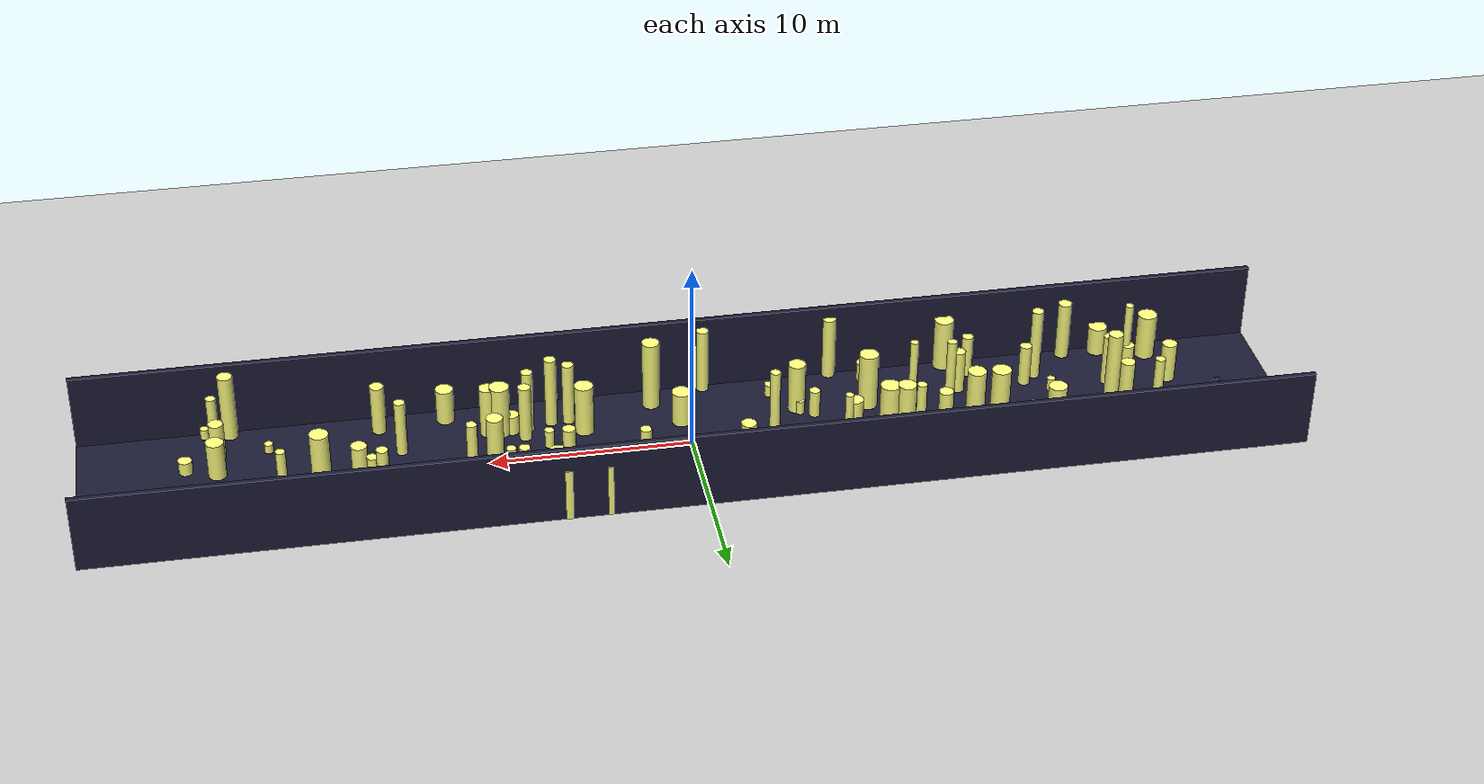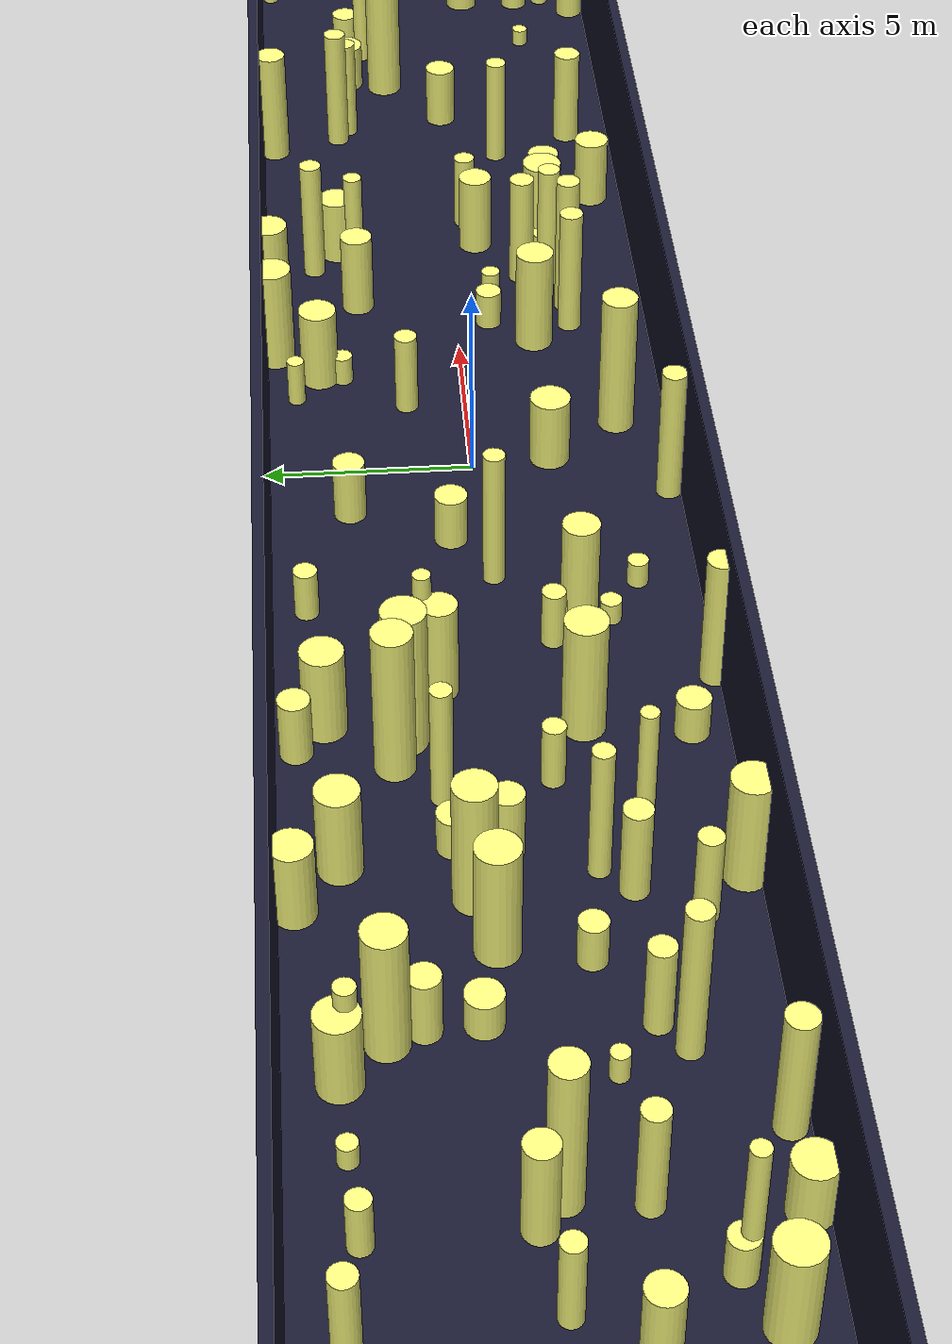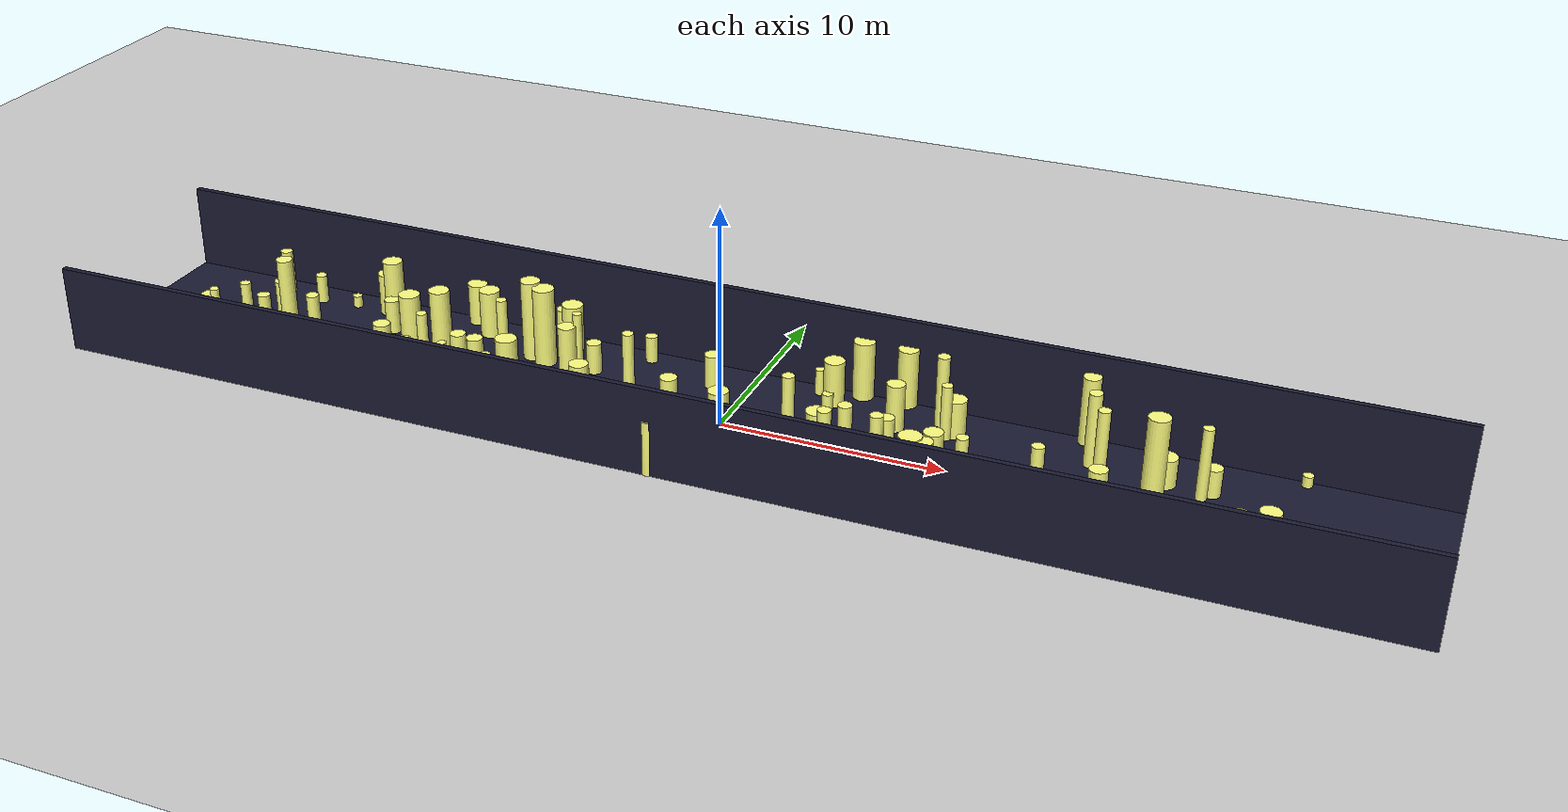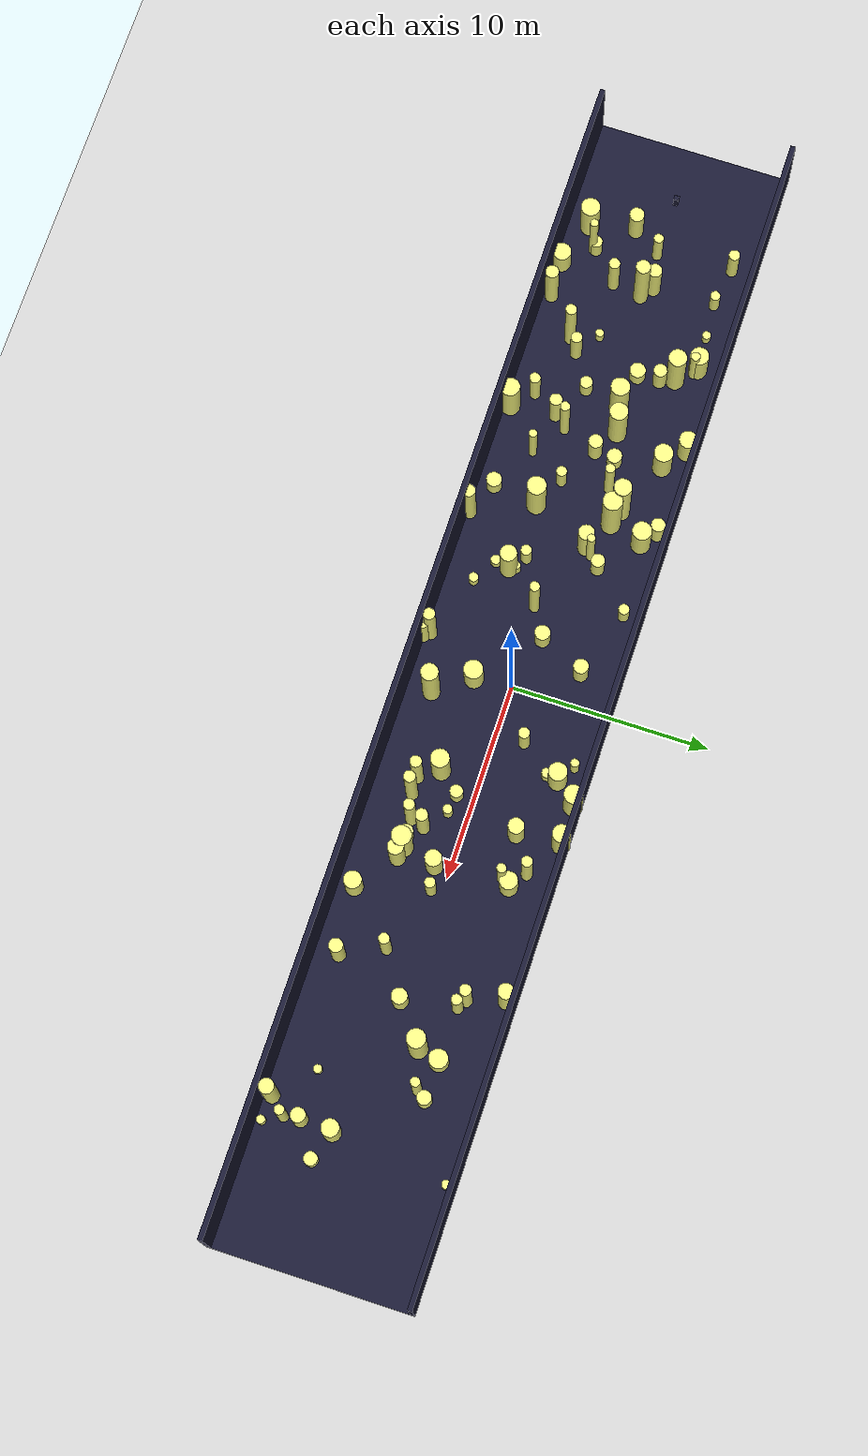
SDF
<?xml version="1.0"?>
<sdf version="1.4">
  <world name="default">
    <gui>
      <camera name="user_camera">
        <pose>-20 -30 40 0 0.66 0.83</pose>
      </camera>
    </gui>
    <include>
      <uri>model://ground_plane</uri>
    </include>
    <include>
      <uri>model://sun</uri>
    </include>
    <scene>
      <shadows>0</shadows>
    </scene>
    <model name="forest">
      <static>true</static>
      <link name="cylinder0">
        <pose>2.5122116245704937 1.4554267723790062 1.0910465891214187 0 0 0 </pose>
        <visual name="visual">
          <geometry>
            <cylinder>
              <radius>0.27874719487534594</radius>
              <length>2.1820931782428374</length>
            </cylinder>
          </geometry>
          <material>
            <ambient>0.6 0.6 0.6 1</ambient>
            <diffuse>1 1 0.5 1</diffuse>
            <specular>0 0 0</specular>
            <emissive>0 0 0 1</emissive>
          </material>
        </visual>
        <collision name="collision">
          <geometry>
            <cylinder>
              <radius>0.27874719487534594</radius>
              <length>2.1820931782428374</length>
            </cylinder>
          </geometry>
          <max_contacts>0</max_contacts>
        </collision>
      </link>
      <link name="cylinder1">
        <pose>5.740298809791739 -2.902266478359432 1.7204444216782937 0 0 0 </pose>
        <visual name="visual">
          <geometry>
            <cylinder>
              <radius>0.29396890148288424</radius>
              <length>3.4408888433565874</length>
            </cylinder>
          </geometry>
          <material>
            <ambient>0.6 0.6 0.6 1</ambient>
            <diffuse>1 1 0.5 1</diffuse>
            <specular>0 0 0</specular>
            <emissive>0 0 0 1</emissive>
          </material>
        </visual>
        <collision name="collision">
          <geometry>
            <cylinder>
              <radius>0.29396890148288424</radius>
              <length>3.4408888433565874</length>
            </cylinder>
          </geometry>
          <max_contacts>0</max_contacts>
        </collision>
      </link>
      <link name="cylinder2">
        <pose>-7.053083177962204 2.1377785248192627 0.7455218717888603 0 0 0 </pose>
        <visual name="visual">
          <geometry>
            <cylinder>
              <radius>0.3425231076029722</radius>
              <length>1.4910437435777206</length>
            </cylinder>
          </geometry>
          <material>
            <ambient>0.6 0.6 0.6 1</ambient>
            <diffuse>1 1 0.5 1</diffuse>
            <specular>0 0 0</specular>
            <emissive>0 0 0 1</emissive>
          </material>
        </visual>
        <collision name="collision">
          <geometry>
            <cylinder>
              <radius>0.3425231076029722</radius>
              <length>1.4910437435777206</length>
            </cylinder>
          </geometry>
          <max_contacts>0</max_contacts>
        </collision>
      </link>
      <link name="cylinder3">
        <pose>15.13735271422376 -3.709229131795847 1.3510711276143499 0 0 0 </pose>
        <visual name="visual">
          <geometry>
            <cylinder>
              <radius>0.349847727589051</radius>
              <length>2.7021422552286998</length>
            </cylinder>
          </geometry>
          <material>
            <ambient>0.6 0.6 0.6 1</ambient>
            <diffuse>1 1 0.5 1</diffuse>
            <specular>0 0 0</specular>
            <emissive>0 0 0 1</emissive>
          </material>
        </visual>
        <collision name="collision">
          <geometry>
            <cylinder>
              <radius>0.349847727589051</radius>
              <length>2.7021422552286998</length>
            </cylinder>
          </geometry>
          <max_contacts>0</max_contacts>
        </collision>
      </link>
      <link name="cylinder4">
        <pose>-4.204448856607289 -0.20657908036231465 1.8052613234034955 0 0 0 </pose>
        <visual name="visual">
          <geometry>
            <cylinder>
              <radius>0.25317556942553027</radius>
              <length>3.610522646806991</length>
            </cylinder>
          </geometry>
          <material>
            <ambient>0.6 0.6 0.6 1</ambient>
            <diffuse>1 1 0.5 1</diffuse>
            <specular>0 0 0</specular>
            <emissive>0 0 0 1</emissive>
          </material>
        </visual>
        <collision name="collision">
          <geometry>
            <cylinder>
              <radius>0.25317556942553027</radius>
              <length>3.610522646806991</length>
            </cylinder>
          </geometry>
          <max_contacts>0</max_contacts>
        </collision>
      </link>
      <link name="cylinder5">
        <pose>9.207790323810706 2.5153890918507305 1.2973155294064729 0 0 0 </pose>
        <visual name="visual">
          <geometry>
            <cylinder>
              <radius>0.23956785812684658</radius>
              <length>2.5946310588129458</length>
            </cylinder>
          </geometry>
          <material>
            <ambient>0.6 0.6 0.6 1</ambient>
            <diffuse>1 1 0.5 1</diffuse>
            <specular>0 0 0</specular>
            <emissive>0 0 0 1</emissive>
          </material>
        </visual>
        <collision name="collision">
          <geometry>
            <cylinder>
              <radius>0.23956785812684658</radius>
              <length>2.5946310588129458</length>
            </cylinder>
          </geometry>
          <max_contacts>0</max_contacts>
        </collision>
      </link>
      <link name="cylinder6">
        <pose>-5.677932761745751 -2.018630922891189 1.3682783342092135 0 0 0 </pose>
        <visual name="visual">
          <geometry>
            <cylinder>
              <radius>0.4287351949719503</radius>
              <length>2.736556668418427</length>
            </cylinder>
          </geometry>
          <material>
            <ambient>0.6 0.6 0.6 1</ambient>
            <diffuse>1 1 0.5 1</diffuse>
            <specular>0 0 0</specular>
            <emissive>0 0 0 1</emissive>
          </material>
        </visual>
        <collision name="collision">
          <geometry>
            <cylinder>
              <radius>0.4287351949719503</radius>
              <length>2.736556668418427</length>
            </cylinder>
          </geometry>
          <max_contacts>0</max_contacts>
        </collision>
      </link>
      <link name="cylinder7">
        <pose>-22.041332455986108 -4.536515657816919 0.778048254228679 0 0 0 </pose>
        <visual name="visual">
          <geometry>
            <cylinder>
              <radius>0.4722223022915783</radius>
              <length>1.556096508457358</length>
            </cylinder>
          </geometry>
          <material>
            <ambient>0.6 0.6 0.6 1</ambient>
            <diffuse>1 1 0.5 1</diffuse>
            <specular>0 0 0</specular>
            <emissive>0 0 0 1</emissive>
          </material>
        </visual>
        <collision name="collision">
          <geometry>
            <cylinder>
              <radius>0.4722223022915783</radius>
              <length>1.556096508457358</length>
            </cylinder>
          </geometry>
          <max_contacts>0</max_contacts>
        </collision>
      </link>
      <link name="cylinder8">
        <pose>-6.470465119566821 -1.3590586940901006 0.7536241077120813 0 0 0 </pose>
        <visual name="visual">
          <geometry>
            <cylinder>
              <radius>0.2710924007848874</radius>
              <length>1.5072482154241627</length>
            </cylinder>
          </geometry>
          <material>
            <ambient>0.6 0.6 0.6 1</ambient>
            <diffuse>1 1 0.5 1</diffuse>
            <specular>0 0 0</specular>
            <emissive>0 0 0 1</emissive>
          </material>
        </visual>
        <collision name="collision">
          <geometry>
            <cylinder>
              <radius>0.2710924007848874</radius>
              <length>1.5072482154241627</length>
            </cylinder>
          </geometry>
          <max_contacts>0</max_contacts>
        </collision>
      </link>
      <link name="cylinder9">
        <pose>-23.257907432206398 -3.105894066248116 0.5873739436395597 0 0 0 </pose>
        <visual name="visual">
          <geometry>
            <cylinder>
              <radius>0.32111720826552903</radius>
              <length>1.1747478872791195</length>
            </cylinder>
          </geometry>
          <material>
            <ambient>0.6 0.6 0.6 1</ambient>
            <diffuse>1 1 0.5 1</diffuse>
            <specular>0 0 0</specular>
            <emissive>0 0 0 1</emissive>
          </material>
        </visual>
        <collision name="collision">
          <geometry>
            <cylinder>
              <radius>0.32111720826552903</radius>
              <length>1.1747478872791195</length>
            </cylinder>
          </geometry>
          <max_contacts>0</max_contacts>
        </collision>
      </link>
      <link name="cylinder10">
        <pose>-10.854893445226294 -0.9547875910160357 0.8113105853004781 0 0 0 </pose>
        <visual name="visual">
          <geometry>
            <cylinder>
              <radius>0.26327560562968627</radius>
              <length>1.6226211706009561</length>
            </cylinder>
          </geometry>
          <material>
            <ambient>0.6 0.6 0.6 1</ambient>
            <diffuse>1 1 0.5 1</diffuse>
            <specular>0 0 0</specular>
            <emissive>0 0 0 1</emissive>
          </material>
        </visual>
        <collision name="collision">
          <geometry>
            <cylinder>
              <radius>0.26327560562968627</radius>
              <length>1.6226211706009561</length>
            </cylinder>
          </geometry>
          <max_contacts>0</max_contacts>
        </collision>
      </link>
      <link name="cylinder11">
        <pose>-10.23968672083252 2.335507035323028 1.9317898075404678 0 0 0 </pose>
        <visual name="visual">
          <geometry>
            <cylinder>
              <radius>0.4478229098009576</radius>
              <length>3.8635796150809356</length>
            </cylinder>
          </geometry>
          <material>
            <ambient>0.6 0.6 0.6 1</ambient>
            <diffuse>1 1 0.5 1</diffuse>
            <specular>0 0 0</specular>
            <emissive>0 0 0 1</emissive>
          </material>
        </visual>
        <collision name="collision">
          <geometry>
            <cylinder>
              <radius>0.4478229098009576</radius>
              <length>3.8635796150809356</length>
            </cylinder>
          </geometry>
          <max_contacts>0</max_contacts>
        </collision>
      </link>
      <link name="cylinder12">
        <pose>-5.794057624121397 -1.644203110581004 0.38806685988691614 0 0 0 </pose>
        <visual name="visual">
          <geometry>
            <cylinder>
              <radius>0.2033211861652654</radius>
              <length>0.7761337197738323</length>
            </cylinder>
          </geometry>
          <material>
            <ambient>0.6 0.6 0.6 1</ambient>
            <diffuse>1 1 0.5 1</diffuse>
            <specular>0 0 0</specular>
            <emissive>0 0 0 1</emissive>
          </material>
        </visual>
        <collision name="collision">
          <geometry>
            <cylinder>
              <radius>0.2033211861652654</radius>
              <length>0.7761337197738323</length>
            </cylinder>
          </geometry>
          <max_contacts>0</max_contacts>
        </collision>
      </link>
      <link name="cylinder13">
        <pose>-17.43027008849827 2.1021531115655083 0.828293583997211 0 0 0 </pose>
        <visual name="visual">
          <geometry>
            <cylinder>
              <radius>0.3463181730629652</radius>
              <length>1.656587167994422</length>
            </cylinder>
          </geometry>
          <material>
            <ambient>0.6 0.6 0.6 1</ambient>
            <diffuse>1 1 0.5 1</diffuse>
            <specular>0 0 0</specular>
            <emissive>0 0 0 1</emissive>
          </material>
        </visual>
        <collision name="collision">
          <geometry>
            <cylinder>
              <radius>0.3463181730629652</radius>
              <length>1.656587167994422</length>
            </cylinder>
          </geometry>
          <max_contacts>0</max_contacts>
        </collision>
      </link>
      <link name="cylinder14">
        <pose>0.18886776030713648 -1.8842476643459873 0.927220741482393 0 0 0 </pose>
        <visual name="visual">
          <geometry>
            <cylinder>
              <radius>0.48721368704605916</radius>
              <length>1.854441482964786</length>
            </cylinder>
          </geometry>
          <material>
            <ambient>0.6 0.6 0.6 1</ambient>
            <diffuse>1 1 0.5 1</diffuse>
            <specular>0 0 0</specular>
            <emissive>0 0 0 1</emissive>
          </material>
        </visual>
        <collision name="collision">
          <geometry>
            <cylinder>
              <radius>0.48721368704605916</radius>
              <length>1.854441482964786</length>
            </cylinder>
          </geometry>
          <max_contacts>0</max_contacts>
        </collision>
      </link>
      <link name="cylinder15">
        <pose>5.080948650887056 -1.9283753831646635 1.3785712172339197 0 0 0 </pose>
        <visual name="visual">
          <geometry>
            <cylinder>
              <radius>0.47102143880978553</radius>
              <length>2.7571424344678395</length>
            </cylinder>
          </geometry>
          <material>
            <ambient>0.6 0.6 0.6 1</ambient>
            <diffuse>1 1 0.5 1</diffuse>
            <specular>0 0 0</specular>
            <emissive>0 0 0 1</emissive>
          </material>
        </visual>
        <collision name="collision">
          <geometry>
            <cylinder>
              <radius>0.47102143880978553</radius>
              <length>2.7571424344678395</length>
            </cylinder>
          </geometry>
          <max_contacts>0</max_contacts>
        </collision>
      </link>
      <link name="cylinder16">
        <pose>6.61182804432131 -2.898672489483226 1.9259601925053633 0 0 0 </pose>
        <visual name="visual">
          <geometry>
            <cylinder>
              <radius>0.29760178141295346</radius>
              <length>3.8519203850107266</length>
            </cylinder>
          </geometry>
          <material>
            <ambient>0.6 0.6 0.6 1</ambient>
            <diffuse>1 1 0.5 1</diffuse>
            <specular>0 0 0</specular>
            <emissive>0 0 0 1</emissive>
          </material>
        </visual>
        <collision name="collision">
          <geometry>
            <cylinder>
              <radius>0.29760178141295346</radius>
              <length>3.8519203850107266</length>
            </cylinder>
          </geometry>
          <max_contacts>0</max_contacts>
        </collision>
      </link>
      <link name="cylinder17">
        <pose>-7.552988100409053 1.5950902559486337 1.542434813002594 0 0 0 </pose>
        <visual name="visual">
          <geometry>
            <cylinder>
              <radius>0.2039629909939676</radius>
              <length>3.084869626005188</length>
            </cylinder>
          </geometry>
          <material>
            <ambient>0.6 0.6 0.6 1</ambient>
            <diffuse>1 1 0.5 1</diffuse>
            <specular>0 0 0</specular>
            <emissive>0 0 0 1</emissive>
          </material>
        </visual>
        <collision name="collision">
          <geometry>
            <cylinder>
              <radius>0.2039629909939676</radius>
              <length>3.084869626005188</length>
            </cylinder>
          </geometry>
          <max_contacts>0</max_contacts>
        </collision>
      </link>
      <link name="cylinder18">
        <pose>-15.87181032003846 -1.2658075620291767 0.5859027005498268 0 0 0 </pose>
        <visual name="visual">
          <geometry>
            <cylinder>
              <radius>0.32011446914979025</radius>
              <length>1.1718054010996537</length>
            </cylinder>
          </geometry>
          <material>
            <ambient>0.6 0.6 0.6 1</ambient>
            <diffuse>1 1 0.5 1</diffuse>
            <specular>0 0 0</specular>
            <emissive>0 0 0 1</emissive>
          </material>
        </visual>
        <collision name="collision">
          <geometry>
            <cylinder>
              <radius>0.32011446914979025</radius>
              <length>1.1718054010996537</length>
            </cylinder>
          </geometry>
          <max_contacts>0</max_contacts>
        </collision>
      </link>
      <link name="cylinder19">
        <pose>-5.1243381241065435 4.093073345648488 0.6514268063172639 0 0 0 </pose>
        <visual name="visual">
          <geometry>
            <cylinder>
              <radius>0.27703393411845423</radius>
              <length>1.3028536126345278</length>
            </cylinder>
          </geometry>
          <material>
            <ambient>0.6 0.6 0.6 1</ambient>
            <diffuse>1 1 0.5 1</diffuse>
            <specular>0 0 0</specular>
            <emissive>0 0 0 1</emissive>
          </material>
        </visual>
        <collision name="collision">
          <geometry>
            <cylinder>
              <radius>0.27703393411845423</radius>
              <length>1.3028536126345278</length>
            </cylinder>
          </geometry>
          <max_contacts>0</max_contacts>
        </collision>
      </link>
      <link name="cylinder20">
        <pose>-20.352650023931176 3.6651285292710423 0.30651279300492185 0 0 0 </pose>
        <visual name="visual">
          <geometry>
            <cylinder>
              <radius>0.2152645864697512</radius>
              <length>0.6130255860098437</length>
            </cylinder>
          </geometry>
          <material>
            <ambient>0.6 0.6 0.6 1</ambient>
            <diffuse>1 1 0.5 1</diffuse>
            <specular>0 0 0</specular>
            <emissive>0 0 0 1</emissive>
          </material>
        </visual>
        <collision name="collision">
          <geometry>
            <cylinder>
              <radius>0.2152645864697512</radius>
              <length>0.6130255860098437</length>
            </cylinder>
          </geometry>
          <max_contacts>0</max_contacts>
        </collision>
      </link>
      <link name="cylinder21">
        <pose>14.794978983714138 4.5721895103297125 1.5877301425671195 0 0 0 </pose>
        <visual name="visual">
          <geometry>
            <cylinder>
              <radius>0.39303448608732106</radius>
              <length>3.175460285134239</length>
            </cylinder>
          </geometry>
          <material>
            <ambient>0.6 0.6 0.6 1</ambient>
            <diffuse>1 1 0.5 1</diffuse>
            <specular>0 0 0</specular>
            <emissive>0 0 0 1</emissive>
          </material>
        </visual>
        <collision name="collision">
          <geometry>
            <cylinder>
              <radius>0.39303448608732106</radius>
              <length>3.175460285134239</length>
            </cylinder>
          </geometry>
          <max_contacts>0</max_contacts>
        </collision>
      </link>
      <link name="cylinder22">
        <pose>1.4580143266485805 -3.6402796680702654 1.8861537415355962 0 0 0 </pose>
        <visual name="visual">
          <geometry>
            <cylinder>
              <radius>0.43752073358639076</radius>
              <length>3.7723074830711925</length>
            </cylinder>
          </geometry>
          <material>
            <ambient>0.6 0.6 0.6 1</ambient>
            <diffuse>1 1 0.5 1</diffuse>
            <specular>0 0 0</specular>
            <emissive>0 0 0 1</emissive>
          </material>
        </visual>
        <collision name="collision">
          <geometry>
            <cylinder>
              <radius>0.43752073358639076</radius>
              <length>3.7723074830711925</length>
            </cylinder>
          </geometry>
          <max_contacts>0</max_contacts>
        </collision>
      </link>
      <link name="cylinder23">
        <pose>-21.722966195620675 -1.6980626440963809 1.389930434521299 0 0 0 </pose>
        <visual name="visual">
          <geometry>
            <cylinder>
              <radius>0.2848266608671214</radius>
              <length>2.779860869042598</length>
            </cylinder>
          </geometry>
          <material>
            <ambient>0.6 0.6 0.6 1</ambient>
            <diffuse>1 1 0.5 1</diffuse>
            <specular>0 0 0</specular>
            <emissive>0 0 0 1</emissive>
          </material>
        </visual>
        <collision name="collision">
          <geometry>
            <cylinder>
              <radius>0.2848266608671214</radius>
              <length>2.779860869042598</length>
            </cylinder>
          </geometry>
          <max_contacts>0</max_contacts>
        </collision>
      </link>
      <link name="cylinder24">
        <pose>2.953514451823768 4.171516001826896 0.6280694018056326 0 0 0 </pose>
        <visual name="visual">
          <geometry>
            <cylinder>
              <radius>0.21291179388986262</radius>
              <length>1.2561388036112653</length>
            </cylinder>
          </geometry>
          <material>
            <ambient>0.6 0.6 0.6 1</ambient>
            <diffuse>1 1 0.5 1</diffuse>
            <specular>0 0 0</specular>
            <emissive>0 0 0 1</emissive>
          </material>
        </visual>
        <collision name="collision">
          <geometry>
            <cylinder>
              <radius>0.21291179388986262</radius>
              <length>1.2561388036112653</length>
            </cylinder>
          </geometry>
          <max_contacts>0</max_contacts>
        </collision>
      </link>
      <link name="cylinder25">
        <pose>-23.93156974054534 -0.05395659627692595 1.1194451601155981 0 0 0 </pose>
        <visual name="visual">
          <geometry>
            <cylinder>
              <radius>0.2484419224223603</radius>
              <length>2.2388903202311963</length>
            </cylinder>
          </geometry>
          <material>
            <ambient>0.6 0.6 0.6 1</ambient>
            <diffuse>1 1 0.5 1</diffuse>
            <specular>0 0 0</specular>
            <emissive>0 0 0 1</emissive>
          </material>
        </visual>
        <collision name="collision">
          <geometry>
            <cylinder>
              <radius>0.2484419224223603</radius>
              <length>2.2388903202311963</length>
            </cylinder>
          </geometry>
          <max_contacts>0</max_contacts>
        </collision>
      </link>
      <link name="cylinder26">
        <pose>-12.838864093144482 0.1674416807421153 0.8606457005123036 0 0 0 </pose>
        <visual name="visual">
          <geometry>
            <cylinder>
              <radius>0.3612265079447227</radius>
              <length>1.7212914010246072</length>
            </cylinder>
          </geometry>
          <material>
            <ambient>0.6 0.6 0.6 1</ambient>
            <diffuse>1 1 0.5 1</diffuse>
            <specular>0 0 0</specular>
            <emissive>0 0 0 1</emissive>
          </material>
        </visual>
        <collision name="collision">
          <geometry>
            <cylinder>
              <radius>0.3612265079447227</radius>
              <length>1.7212914010246072</length>
            </cylinder>
          </geometry>
          <max_contacts>0</max_contacts>
        </collision>
      </link>
      <link name="cylinder27">
        <pose>16.339308908062087 -0.2025547932904317 0.8571047263075176 0 0 0 </pose>
        <visual name="visual">
          <geometry>
            <cylinder>
              <radius>0.39997915163697584</radius>
              <length>1.714209452615035</length>
            </cylinder>
          </geometry>
          <material>
            <ambient>0.6 0.6 0.6 1</ambient>
            <diffuse>1 1 0.5 1</diffuse>
            <specular>0 0 0</specular>
            <emissive>0 0 0 1</emissive>
          </material>
        </visual>
        <collision name="collision">
          <geometry>
            <cylinder>
              <radius>0.39997915163697584</radius>
              <length>1.714209452615035</length>
            </cylinder>
          </geometry>
          <max_contacts>0</max_contacts>
        </collision>
      </link>
      <link name="cylinder28">
        <pose>-14.86856106425778 -3.635986227326521 1.1519740065115995 0 0 0 </pose>
        <visual name="visual">
          <geometry>
            <cylinder>
              <radius>0.27546447704839416</radius>
              <length>2.303948013023199</length>
            </cylinder>
          </geometry>
          <material>
            <ambient>0.6 0.6 0.6 1</ambient>
            <diffuse>1 1 0.5 1</diffuse>
            <specular>0 0 0</specular>
            <emissive>0 0 0 1</emissive>
          </material>
        </visual>
        <collision name="collision">
          <geometry>
            <cylinder>
              <radius>0.27546447704839416</radius>
              <length>2.303948013023199</length>
            </cylinder>
          </geometry>
          <max_contacts>0</max_contacts>
        </collision>
      </link>
      <link name="cylinder29">
        <pose>-20.171636058569163 -4.477696496845774 1.5868214042546143 0 0 0 </pose>
        <visual name="visual">
          <geometry>
            <cylinder>
              <radius>0.33702319453878626</radius>
              <length>3.1736428085092285</length>
            </cylinder>
          </geometry>
          <material>
            <ambient>0.6 0.6 0.6 1</ambient>
            <diffuse>1 1 0.5 1</diffuse>
            <specular>0 0 0</specular>
            <emissive>0 0 0 1</emissive>
          </material>
        </visual>
        <collision name="collision">
          <geometry>
            <cylinder>
              <radius>0.33702319453878626</radius>
              <length>3.1736428085092285</length>
            </cylinder>
          </geometry>
          <max_contacts>0</max_contacts>
        </collision>
      </link>
      <link name="cylinder30">
        <pose>-7.916161896281217 1.2496600140404208 1.2726255154498964 0 0 0 </pose>
        <visual name="visual">
          <geometry>
            <cylinder>
              <radius>0.4072249907252693</radius>
              <length>2.545251030899793</length>
            </cylinder>
          </geometry>
          <material>
            <ambient>0.6 0.6 0.6 1</ambient>
            <diffuse>1 1 0.5 1</diffuse>
            <specular>0 0 0</specular>
            <emissive>0 0 0 1</emissive>
          </material>
        </visual>
        <collision name="collision">
          <geometry>
            <cylinder>
              <radius>0.4072249907252693</radius>
              <length>2.545251030899793</length>
            </cylinder>
          </geometry>
          <max_contacts>0</max_contacts>
        </collision>
      </link>
      <link name="cylinder31">
        <pose>-17.70354404161665 2.8310066277029486 1.6273444225232137 0 0 0 </pose>
        <visual name="visual">
          <geometry>
            <cylinder>
              <radius>0.4597115606962541</radius>
              <length>3.2546888450464273</length>
            </cylinder>
          </geometry>
          <material>
            <ambient>0.6 0.6 0.6 1</ambient>
            <diffuse>1 1 0.5 1</diffuse>
            <specular>0 0 0</specular>
            <emissive>0 0 0 1</emissive>
          </material>
        </visual>
        <collision name="collision">
          <geometry>
            <cylinder>
              <radius>0.4597115606962541</radius>
              <length>3.2546888450464273</length>
            </cylinder>
          </geometry>
          <max_contacts>0</max_contacts>
        </collision>
      </link>
      <link name="cylinder32">
        <pose>-9.281641906676663 -1.7557040595859674 1.5452566506517336 0 0 0 </pose>
        <visual name="visual">
          <geometry>
            <cylinder>
              <radius>0.48616027494389596</radius>
              <length>3.090513301303467</length>
            </cylinder>
          </geometry>
          <material>
            <ambient>0.6 0.6 0.6 1</ambient>
            <diffuse>1 1 0.5 1</diffuse>
            <specular>0 0 0</specular>
            <emissive>0 0 0 1</emissive>
          </material>
        </visual>
        <collision name="collision">
          <geometry>
            <cylinder>
              <radius>0.48616027494389596</radius>
              <length>3.090513301303467</length>
            </cylinder>
          </geometry>
          <max_contacts>0</max_contacts>
        </collision>
      </link>
      <link name="cylinder33">
        <pose>18.23974290360573 1.339459283368205 1.8441640490602003 0 0 0 </pose>
        <visual name="visual">
          <geometry>
            <cylinder>
              <radius>0.47264410393034395</radius>
              <length>3.6883280981204005</length>
            </cylinder>
          </geometry>
          <material>
            <ambient>0.6 0.6 0.6 1</ambient>
            <diffuse>1 1 0.5 1</diffuse>
            <specular>0 0 0</specular>
            <emissive>0 0 0 1</emissive>
          </material>
        </visual>
        <collision name="collision">
          <geometry>
            <cylinder>
              <radius>0.47264410393034395</radius>
              <length>3.6883280981204005</length>
            </cylinder>
          </geometry>
          <max_contacts>0</max_contacts>
        </collision>
      </link>
      <link name="cylinder34">
        <pose>23.095826558992556 -2.8613568608352025 0.9951352167996178 0 0 0 </pose>
        <visual name="visual">
          <geometry>
            <cylinder>
              <radius>0.3710210629821359</radius>
              <length>1.9902704335992356</length>
            </cylinder>
          </geometry>
          <material>
            <ambient>0.6 0.6 0.6 1</ambient>
            <diffuse>1 1 0.5 1</diffuse>
            <specular>0 0 0</specular>
            <emissive>0 0 0 1</emissive>
          </material>
        </visual>
        <collision name="collision">
          <geometry>
            <cylinder>
              <radius>0.3710210629821359</radius>
              <length>1.9902704335992356</length>
            </cylinder>
          </geometry>
          <max_contacts>0</max_contacts>
        </collision>
      </link>
      <link name="cylinder35">
        <pose>24.714990797352712 -1.765484414521131 0.38211233775964437 0 0 0 </pose>
        <visual name="visual">
          <geometry>
            <cylinder>
              <radius>0.3425147693579313</radius>
              <length>0.7642246755192887</length>
            </cylinder>
          </geometry>
          <material>
            <ambient>0.6 0.6 0.6 1</ambient>
            <diffuse>1 1 0.5 1</diffuse>
            <specular>0 0 0</specular>
            <emissive>0 0 0 1</emissive>
          </material>
        </visual>
        <collision name="collision">
          <geometry>
            <cylinder>
              <radius>0.3425147693579313</radius>
              <length>0.7642246755192887</length>
            </cylinder>
          </geometry>
          <max_contacts>0</max_contacts>
        </collision>
      </link>
      <link name="cylinder36">
        <pose>23.224490616280995 -3.663025094059953 1.477940125006662 0 0 0 </pose>
        <visual name="visual">
          <geometry>
            <cylinder>
              <radius>0.24628033705042934</radius>
              <length>2.955880250013324</length>
            </cylinder>
          </geometry>
          <material>
            <ambient>0.6 0.6 0.6 1</ambient>
            <diffuse>1 1 0.5 1</diffuse>
            <specular>0 0 0</specular>
            <emissive>0 0 0 1</emissive>
          </material>
        </visual>
        <collision name="collision">
          <geometry>
            <cylinder>
              <radius>0.24628033705042934</radius>
              <length>2.955880250013324</length>
            </cylinder>
          </geometry>
          <max_contacts>0</max_contacts>
        </collision>
      </link>
      <link name="cylinder37">
        <pose>8.032982198013158 -1.8444594471032048 1.5328081589239524 0 0 0 </pose>
        <visual name="visual">
          <geometry>
            <cylinder>
              <radius>0.31196018191229113</radius>
              <length>3.065616317847905</length>
            </cylinder>
          </geometry>
          <material>
            <ambient>0.6 0.6 0.6 1</ambient>
            <diffuse>1 1 0.5 1</diffuse>
            <specular>0 0 0</specular>
            <emissive>0 0 0 1</emissive>
          </material>
        </visual>
        <collision name="collision">
          <geometry>
            <cylinder>
              <radius>0.31196018191229113</radius>
              <length>3.065616317847905</length>
            </cylinder>
          </geometry>
          <max_contacts>0</max_contacts>
        </collision>
      </link>
      <link name="cylinder38">
        <pose>-9.668939333349218 4.412859585392857 0.8135028487092946 0 0 0 </pose>
        <visual name="visual">
          <geometry>
            <cylinder>
              <radius>0.3592106942418169</radius>
              <length>1.6270056974185891</length>
            </cylinder>
          </geometry>
          <material>
            <ambient>0.6 0.6 0.6 1</ambient>
            <diffuse>1 1 0.5 1</diffuse>
            <specular>0 0 0</specular>
            <emissive>0 0 0 1</emissive>
          </material>
        </visual>
        <collision name="collision">
          <geometry>
            <cylinder>
              <radius>0.3592106942418169</radius>
              <length>1.6270056974185891</length>
            </cylinder>
          </geometry>
          <max_contacts>0</max_contacts>
        </collision>
      </link>
      <link name="cylinder39">
        <pose>-17.35243403862967 0.9638053620396594 0.4821447008460237 0 0 0 </pose>
        <visual name="visual">
          <geometry>
            <cylinder>
              <radius>0.40450242599011765</radius>
              <length>0.9642894016920474</length>
            </cylinder>
          </geometry>
          <material>
            <ambient>0.6 0.6 0.6 1</ambient>
            <diffuse>1 1 0.5 1</diffuse>
            <specular>0 0 0</specular>
            <emissive>0 0 0 1</emissive>
          </material>
        </visual>
        <collision name="collision">
          <geometry>
            <cylinder>
              <radius>0.40450242599011765</radius>
              <length>0.9642894016920474</length>
            </cylinder>
          </geometry>
          <max_contacts>0</max_contacts>
        </collision>
      </link>
      <link name="cylinder40">
        <pose>-8.921030794987683 3.7843819762125275 1.137610614174596 0 0 0 </pose>
        <visual name="visual">
          <geometry>
            <cylinder>
              <radius>0.48728707302580004</radius>
              <length>2.275221228349192</length>
            </cylinder>
          </geometry>
          <material>
            <ambient>0.6 0.6 0.6 1</ambient>
            <diffuse>1 1 0.5 1</diffuse>
            <specular>0 0 0</specular>
            <emissive>0 0 0 1</emissive>
          </material>
        </visual>
        <collision name="collision">
          <geometry>
            <cylinder>
              <radius>0.48728707302580004</radius>
              <length>2.275221228349192</length>
            </cylinder>
          </geometry>
          <max_contacts>0</max_contacts>
        </collision>
      </link>
      <link name="cylinder41">
        <pose>-15.491157676276757 0.5705804064977293 1.4863054029059948 0 0 0 </pose>
        <visual name="visual">
          <geometry>
            <cylinder>
              <radius>0.48136702820251775</radius>
              <length>2.9726108058119896</length>
            </cylinder>
          </geometry>
          <material>
            <ambient>0.6 0.6 0.6 1</ambient>
            <diffuse>1 1 0.5 1</diffuse>
            <specular>0 0 0</specular>
            <emissive>0 0 0 1</emissive>
          </material>
        </visual>
        <collision name="collision">
          <geometry>
            <cylinder>
              <radius>0.48136702820251775</radius>
              <length>2.9726108058119896</length>
            </cylinder>
          </geometry>
          <max_contacts>0</max_contacts>
        </collision>
      </link>
      <link name="cylinder42">
        <pose>4.786974622643086 4.668397056595717 1.3857671620983145 0 0 0 </pose>
        <visual name="visual">
          <geometry>
            <cylinder>
              <radius>0.47808542402327797</radius>
              <length>2.771534324196629</length>
            </cylinder>
          </geometry>
          <material>
            <ambient>0.6 0.6 0.6 1</ambient>
            <diffuse>1 1 0.5 1</diffuse>
            <specular>0 0 0</specular>
            <emissive>0 0 0 1</emissive>
          </material>
        </visual>
        <collision name="collision">
          <geometry>
            <cylinder>
              <radius>0.47808542402327797</radius>
              <length>2.771534324196629</length>
            </cylinder>
          </geometry>
          <max_contacts>0</max_contacts>
        </collision>
      </link>
      <link name="cylinder43">
        <pose>-11.227578387033772 1.403979539215511 1.5701394048374335 0 0 0 </pose>
        <visual name="visual">
          <geometry>
            <cylinder>
              <radius>0.24317565934227597</radius>
              <length>3.140278809674867</length>
            </cylinder>
          </geometry>
          <material>
            <ambient>0.6 0.6 0.6 1</ambient>
            <diffuse>1 1 0.5 1</diffuse>
            <specular>0 0 0</specular>
            <emissive>0 0 0 1</emissive>
          </material>
        </visual>
        <collision name="collision">
          <geometry>
            <cylinder>
              <radius>0.24317565934227597</radius>
              <length>3.140278809674867</length>
            </cylinder>
          </geometry>
          <max_contacts>0</max_contacts>
        </collision>
      </link>
      <link name="cylinder44">
        <pose>6.970719649108322 2.507995609290621 1.1072151191163275 0 0 0 </pose>
        <visual name="visual">
          <geometry>
            <cylinder>
              <radius>0.40269769239476133</radius>
              <length>2.214430238232655</length>
            </cylinder>
          </geometry>
          <material>
            <ambient>0.6 0.6 0.6 1</ambient>
            <diffuse>1 1 0.5 1</diffuse>
            <specular>0 0 0</specular>
            <emissive>0 0 0 1</emissive>
          </material>
        </visual>
        <collision name="collision">
          <geometry>
            <cylinder>
              <radius>0.40269769239476133</radius>
              <length>2.214430238232655</length>
            </cylinder>
          </geometry>
          <max_contacts>0</max_contacts>
        </collision>
      </link>
      <link name="cylinder45">
        <pose>15.831610690590296 2.4912157370991554 1.4367248032020083 0 0 0 </pose>
        <visual name="visual">
          <geometry>
            <cylinder>
              <radius>0.26768839269387523</radius>
              <length>2.8734496064040167</length>
            </cylinder>
          </geometry>
          <material>
            <ambient>0.6 0.6 0.6 1</ambient>
            <diffuse>1 1 0.5 1</diffuse>
            <specular>0 0 0</specular>
            <emissive>0 0 0 1</emissive>
          </material>
        </visual>
        <collision name="collision">
          <geometry>
            <cylinder>
              <radius>0.26768839269387523</radius>
              <length>2.8734496064040167</length>
            </cylinder>
          </geometry>
          <max_contacts>0</max_contacts>
        </collision>
      </link>
      <link name="cylinder46">
        <pose>-24.267590009946556 3.8172753181171313 1.0849845144291745 0 0 0 </pose>
        <visual name="visual">
          <geometry>
            <cylinder>
              <radius>0.28195847940675284</radius>
              <length>2.169969028858349</length>
            </cylinder>
          </geometry>
          <material>
            <ambient>0.6 0.6 0.6 1</ambient>
            <diffuse>1 1 0.5 1</diffuse>
            <specular>0 0 0</specular>
            <emissive>0 0 0 1</emissive>
          </material>
        </visual>
        <collision name="collision">
          <geometry>
            <cylinder>
              <radius>0.28195847940675284</radius>
              <length>2.169969028858349</length>
            </cylinder>
          </geometry>
          <max_contacts>0</max_contacts>
        </collision>
      </link>
      <link name="cylinder47">
        <pose>-13.501873059228553 -1.650667561456686 1.7129860077275327 0 0 0 </pose>
        <visual name="visual">
          <geometry>
            <cylinder>
              <radius>0.24190093716637934</radius>
              <length>3.4259720154550655</length>
            </cylinder>
          </geometry>
          <material>
            <ambient>0.6 0.6 0.6 1</ambient>
            <diffuse>1 1 0.5 1</diffuse>
            <specular>0 0 0</specular>
            <emissive>0 0 0 1</emissive>
          </material>
        </visual>
        <collision name="collision">
          <geometry>
            <cylinder>
              <radius>0.24190093716637934</radius>
              <length>3.4259720154550655</length>
            </cylinder>
          </geometry>
          <max_contacts>0</max_contacts>
        </collision>
      </link>
      <link name="cylinder48">
        <pose>7.819350977288607 -2.5271675822177464 1.7340828750675485 0 0 0 </pose>
        <visual name="visual">
          <geometry>
            <cylinder>
              <radius>0.2831108168849127</radius>
              <length>3.468165750135097</length>
            </cylinder>
          </geometry>
          <material>
            <ambient>0.6 0.6 0.6 1</ambient>
            <diffuse>1 1 0.5 1</diffuse>
            <specular>0 0 0</specular>
            <emissive>0 0 0 1</emissive>
          </material>
        </visual>
        <collision name="collision">
          <geometry>
            <cylinder>
              <radius>0.2831108168849127</radius>
              <length>3.468165750135097</length>
            </cylinder>
          </geometry>
          <max_contacts>0</max_contacts>
        </collision>
      </link>
      <link name="cylinder49">
        <pose>22.448143988832122 -4.504987331807815 1.8040991506452526 0 0 0 </pose>
        <visual name="visual">
          <geometry>
            <cylinder>
              <radius>0.3788110216736742</radius>
              <length>3.6081983012905052</length>
            </cylinder>
          </geometry>
          <material>
            <ambient>0.6 0.6 0.6 1</ambient>
            <diffuse>1 1 0.5 1</diffuse>
            <specular>0 0 0</specular>
            <emissive>0 0 0 1</emissive>
          </material>
        </visual>
        <collision name="collision">
          <geometry>
            <cylinder>
              <radius>0.3788110216736742</radius>
              <length>3.6081983012905052</length>
            </cylinder>
          </geometry>
          <max_contacts>0</max_contacts>
        </collision>
      </link>
      <link name="cylinder50">
        <pose>9.221202019788997 -2.4680737388358143 1.407225930817046 0 0 0 </pose>
        <visual name="visual">
          <geometry>
            <cylinder>
              <radius>0.49617912433899053</radius>
              <length>2.814451861634092</length>
            </cylinder>
          </geometry>
          <material>
            <ambient>0.6 0.6 0.6 1</ambient>
            <diffuse>1 1 0.5 1</diffuse>
            <specular>0 0 0</specular>
            <emissive>0 0 0 1</emissive>
          </material>
        </visual>
        <collision name="collision">
          <geometry>
            <cylinder>
              <radius>0.49617912433899053</radius>
              <length>2.814451861634092</length>
            </cylinder>
          </geometry>
          <max_contacts>0</max_contacts>
        </collision>
      </link>
      <link name="cylinder51">
        <pose>23.20490847644362 -1.2479280300506157 1.0096954887568317 0 0 0 </pose>
        <visual name="visual">
          <geometry>
            <cylinder>
              <radius>0.4433873506201335</radius>
              <length>2.0193909775136634</length>
            </cylinder>
          </geometry>
          <material>
            <ambient>0.6 0.6 0.6 1</ambient>
            <diffuse>1 1 0.5 1</diffuse>
            <specular>0 0 0</specular>
            <emissive>0 0 0 1</emissive>
          </material>
        </visual>
        <collision name="collision">
          <geometry>
            <cylinder>
              <radius>0.4433873506201335</radius>
              <length>2.0193909775136634</length>
            </cylinder>
          </geometry>
          <max_contacts>0</max_contacts>
        </collision>
      </link>
      <link name="cylinder52">
        <pose>-13.95625358361427 -4.569633419246502 0.8893343200442988 0 0 0 </pose>
        <visual name="visual">
          <geometry>
            <cylinder>
              <radius>0.3392188028762888</radius>
              <length>1.7786686400885976</length>
            </cylinder>
          </geometry>
          <material>
            <ambient>0.6 0.6 0.6 1</ambient>
            <diffuse>1 1 0.5 1</diffuse>
            <specular>0 0 0</specular>
            <emissive>0 0 0 1</emissive>
          </material>
        </visual>
        <collision name="collision">
          <geometry>
            <cylinder>
              <radius>0.3392188028762888</radius>
              <length>1.7786686400885976</length>
            </cylinder>
          </geometry>
          <max_contacts>0</max_contacts>
        </collision>
      </link>
      <link name="cylinder53">
        <pose>20.10760565190381 1.9123318650157275 1.6537855213037769 0 0 0 </pose>
        <visual name="visual">
          <geometry>
            <cylinder>
              <radius>0.2386102407152301</radius>
              <length>3.3075710426075537</length>
            </cylinder>
          </geometry>
          <material>
            <ambient>0.6 0.6 0.6 1</ambient>
            <diffuse>1 1 0.5 1</diffuse>
            <specular>0 0 0</specular>
            <emissive>0 0 0 1</emissive>
          </material>
        </visual>
        <collision name="collision">
          <geometry>
            <cylinder>
              <radius>0.2386102407152301</radius>
              <length>3.3075710426075537</length>
            </cylinder>
          </geometry>
          <max_contacts>0</max_contacts>
        </collision>
      </link>
      <link name="cylinder54">
        <pose>-24.87595430924636 -1.4902560423669775 1.066712900287382 0 0 0 </pose>
        <visual name="visual">
          <geometry>
            <cylinder>
              <radius>0.38071903366398585</radius>
              <length>2.133425800574764</length>
            </cylinder>
          </geometry>
          <material>
            <ambient>0.6 0.6 0.6 1</ambient>
            <diffuse>1 1 0.5 1</diffuse>
            <specular>0 0 0</specular>
            <emissive>0 0 0 1</emissive>
          </material>
        </visual>
        <collision name="collision">
          <geometry>
            <cylinder>
              <radius>0.38071903366398585</radius>
              <length>2.133425800574764</length>
            </cylinder>
          </geometry>
          <max_contacts>0</max_contacts>
        </collision>
      </link>
      <link name="cylinder55">
        <pose>-7.902964053480538 -4.777170698010959 1.708010642592269 0 0 0 </pose>
        <visual name="visual">
          <geometry>
            <cylinder>
              <radius>0.3296761939961388</radius>
              <length>3.416021285184538</length>
            </cylinder>
          </geometry>
          <material>
            <ambient>0.6 0.6 0.6 1</ambient>
            <diffuse>1 1 0.5 1</diffuse>
            <specular>0 0 0</specular>
            <emissive>0 0 0 1</emissive>
          </material>
        </visual>
        <collision name="collision">
          <geometry>
            <cylinder>
              <radius>0.3296761939961388</radius>
              <length>3.416021285184538</length>
            </cylinder>
          </geometry>
          <max_contacts>0</max_contacts>
        </collision>
      </link>
      <link name="cylinder56">
        <pose>-17.574686243195902 -2.349012793082077 1.1330386439145852 0 0 0 </pose>
        <visual name="visual">
          <geometry>
            <cylinder>
              <radius>0.29526821620431387</radius>
              <length>2.2660772878291704</length>
            </cylinder>
          </geometry>
          <material>
            <ambient>0.6 0.6 0.6 1</ambient>
            <diffuse>1 1 0.5 1</diffuse>
            <specular>0 0 0</specular>
            <emissive>0 0 0 1</emissive>
          </material>
        </visual>
        <collision name="collision">
          <geometry>
            <cylinder>
              <radius>0.29526821620431387</radius>
              <length>2.2660772878291704</length>
            </cylinder>
          </geometry>
          <max_contacts>0</max_contacts>
        </collision>
      </link>
      <link name="cylinder57">
        <pose>9.809432336711879 -2.5612738248359515 1.3699632924031055 0 0 0 </pose>
        <visual name="visual">
          <geometry>
            <cylinder>
              <radius>0.40042244446624675</radius>
              <length>2.739926584806211</length>
            </cylinder>
          </geometry>
          <material>
            <ambient>0.6 0.6 0.6 1</ambient>
            <diffuse>1 1 0.5 1</diffuse>
            <specular>0 0 0</specular>
            <emissive>0 0 0 1</emissive>
          </material>
        </visual>
        <collision name="collision">
          <geometry>
            <cylinder>
              <radius>0.40042244446624675</radius>
              <length>2.739926584806211</length>
            </cylinder>
          </geometry>
          <max_contacts>0</max_contacts>
        </collision>
      </link>
      <link name="cylinder58">
        <pose>-14.123253541562036 0.9191090500755568 1.6398232900675318 0 0 0 </pose>
        <visual name="visual">
          <geometry>
            <cylinder>
              <radius>0.46551618750189744</radius>
              <length>3.2796465801350636</length>
            </cylinder>
          </geometry>
          <material>
            <ambient>0.6 0.6 0.6 1</ambient>
            <diffuse>1 1 0.5 1</diffuse>
            <specular>0 0 0</specular>
            <emissive>0 0 0 1</emissive>
          </material>
        </visual>
        <collision name="collision">
          <geometry>
            <cylinder>
              <radius>0.46551618750189744</radius>
              <length>3.2796465801350636</length>
            </cylinder>
          </geometry>
          <max_contacts>0</max_contacts>
        </collision>
      </link>
      <link name="cylinder59">
        <pose>-9.609776152343997 -4.061012149677348 0.5256643369051615 0 0 0 </pose>
        <visual name="visual">
          <geometry>
            <cylinder>
              <radius>0.3874751381393938</radius>
              <length>1.051328673810323</length>
            </cylinder>
          </geometry>
          <material>
            <ambient>0.6 0.6 0.6 1</ambient>
            <diffuse>1 1 0.5 1</diffuse>
            <specular>0 0 0</specular>
            <emissive>0 0 0 1</emissive>
          </material>
        </visual>
        <collision name="collision">
          <geometry>
            <cylinder>
              <radius>0.3874751381393938</radius>
              <length>1.051328673810323</length>
            </cylinder>
          </geometry>
          <max_contacts>0</max_contacts>
        </collision>
      </link>
      <link name="cylinder60">
        <pose>-9.456611717616886 2.0667098246911006 1.8742407907984417 0 0 0 </pose>
        <visual name="visual">
          <geometry>
            <cylinder>
              <radius>0.49501910202960187</radius>
              <length>3.7484815815968835</length>
            </cylinder>
          </geometry>
          <material>
            <ambient>0.6 0.6 0.6 1</ambient>
            <diffuse>1 1 0.5 1</diffuse>
            <specular>0 0 0</specular>
            <emissive>0 0 0 1</emissive>
          </material>
        </visual>
        <collision name="collision">
          <geometry>
            <cylinder>
              <radius>0.49501910202960187</radius>
              <length>3.7484815815968835</length>
            </cylinder>
          </geometry>
          <max_contacts>0</max_contacts>
        </collision>
      </link>
      <link name="cylinder61">
        <pose>-11.872005867686536 -2.7799893459832283 1.4228996720215508 0 0 0 </pose>
        <visual name="visual">
          <geometry>
            <cylinder>
              <radius>0.20490631877437468</radius>
              <length>2.8457993440431015</length>
            </cylinder>
          </geometry>
          <material>
            <ambient>0.6 0.6 0.6 1</ambient>
            <diffuse>1 1 0.5 1</diffuse>
            <specular>0 0 0</specular>
            <emissive>0 0 0 1</emissive>
          </material>
        </visual>
        <collision name="collision">
          <geometry>
            <cylinder>
              <radius>0.20490631877437468</radius>
              <length>2.8457993440431015</length>
            </cylinder>
          </geometry>
          <max_contacts>0</max_contacts>
        </collision>
      </link>
      <link name="cylinder62">
        <pose>-1.1202543328110366 -4.891617807019855 1.2433011680831552 0 0 0 </pose>
        <visual name="visual">
          <geometry>
            <cylinder>
              <radius>0.2914426185208163</radius>
              <length>2.4866023361663103</length>
            </cylinder>
          </geometry>
          <material>
            <ambient>0.6 0.6 0.6 1</ambient>
            <diffuse>1 1 0.5 1</diffuse>
            <specular>0 0 0</specular>
            <emissive>0 0 0 1</emissive>
          </material>
        </visual>
        <collision name="collision">
          <geometry>
            <cylinder>
              <radius>0.2914426185208163</radius>
              <length>2.4866023361663103</length>
            </cylinder>
          </geometry>
          <max_contacts>0</max_contacts>
        </collision>
      </link>
      <link name="cylinder63">
        <pose>3.8190027920107568 3.579123430146577 1.074971093633638 0 0 0 </pose>
        <visual name="visual">
          <geometry>
            <cylinder>
              <radius>0.4647251919647949</radius>
              <length>2.149942187267276</length>
            </cylinder>
          </geometry>
          <material>
            <ambient>0.6 0.6 0.6 1</ambient>
            <diffuse>1 1 0.5 1</diffuse>
            <specular>0 0 0</specular>
            <emissive>0 0 0 1</emissive>
          </material>
        </visual>
        <collision name="collision">
          <geometry>
            <cylinder>
              <radius>0.4647251919647949</radius>
              <length>2.149942187267276</length>
            </cylinder>
          </geometry>
          <max_contacts>0</max_contacts>
        </collision>
      </link>
      <link name="cylinder64">
        <pose>-1.3353628650063172 -4.603153292782719 1.7711445876848795 0 0 0 </pose>
        <visual name="visual">
          <geometry>
            <cylinder>
              <radius>0.30010122480529033</radius>
              <length>3.542289175369759</length>
            </cylinder>
          </geometry>
          <material>
            <ambient>0.6 0.6 0.6 1</ambient>
            <diffuse>1 1 0.5 1</diffuse>
            <specular>0 0 0</specular>
            <emissive>0 0 0 1</emissive>
          </material>
        </visual>
        <collision name="collision">
          <geometry>
            <cylinder>
              <radius>0.30010122480529033</radius>
              <length>3.542289175369759</length>
            </cylinder>
          </geometry>
          <max_contacts>0</max_contacts>
        </collision>
      </link>
      <link name="cylinder65">
        <pose>-1.6459123704790137 2.9986343947005736 0.799410165478372 0 0 0 </pose>
        <visual name="visual">
          <geometry>
            <cylinder>
              <radius>0.379796284494472</radius>
              <length>1.598820330956744</length>
            </cylinder>
          </geometry>
          <material>
            <ambient>0.6 0.6 0.6 1</ambient>
            <diffuse>1 1 0.5 1</diffuse>
            <specular>0 0 0</specular>
            <emissive>0 0 0 1</emissive>
          </material>
        </visual>
        <collision name="collision">
          <geometry>
            <cylinder>
              <radius>0.379796284494472</radius>
              <length>1.598820330956744</length>
            </cylinder>
          </geometry>
          <max_contacts>0</max_contacts>
        </collision>
      </link>
      <link name="cylinder66">
        <pose>-13.088519057582577 3.5834655569239473 1.153539882643262 0 0 0 </pose>
        <visual name="visual">
          <geometry>
            <cylinder>
              <radius>0.4778429957184916</radius>
              <length>2.307079765286524</length>
            </cylinder>
          </geometry>
          <material>
            <ambient>0.6 0.6 0.6 1</ambient>
            <diffuse>1 1 0.5 1</diffuse>
            <specular>0 0 0</specular>
            <emissive>0 0 0 1</emissive>
          </material>
        </visual>
        <collision name="collision">
          <geometry>
            <cylinder>
              <radius>0.4778429957184916</radius>
              <length>2.307079765286524</length>
            </cylinder>
          </geometry>
          <max_contacts>0</max_contacts>
        </collision>
      </link>
      <link name="cylinder67">
        <pose>10.817768553214854 -0.5259603936769741 1.039585505066491 0 0 0 </pose>
        <visual name="visual">
          <geometry>
            <cylinder>
              <radius>0.26878573653986737</radius>
              <length>2.079171010132982</length>
            </cylinder>
          </geometry>
          <material>
            <ambient>0.6 0.6 0.6 1</ambient>
            <diffuse>1 1 0.5 1</diffuse>
            <specular>0 0 0</specular>
            <emissive>0 0 0 1</emissive>
          </material>
        </visual>
        <collision name="collision">
          <geometry>
            <cylinder>
              <radius>0.26878573653986737</radius>
              <length>2.079171010132982</length>
            </cylinder>
          </geometry>
          <max_contacts>0</max_contacts>
        </collision>
      </link>
      <link name="cylinder68">
        <pose>14.183803024570182 -1.6321367324853906 1.5153235489839836 0 0 0 </pose>
        <visual name="visual">
          <geometry>
            <cylinder>
              <radius>0.27197004012225234</radius>
              <length>3.030647097967967</length>
            </cylinder>
          </geometry>
          <material>
            <ambient>0.6 0.6 0.6 1</ambient>
            <diffuse>1 1 0.5 1</diffuse>
            <specular>0 0 0</specular>
            <emissive>0 0 0 1</emissive>
          </material>
        </visual>
        <collision name="collision">
          <geometry>
            <cylinder>
              <radius>0.27197004012225234</radius>
              <length>3.030647097967967</length>
            </cylinder>
          </geometry>
          <max_contacts>0</max_contacts>
        </collision>
      </link>
      <link name="cylinder69">
        <pose>20.631126038959664 -2.8458166371514038 0.26310570461469074 0 0 0 </pose>
        <visual name="visual">
          <geometry>
            <cylinder>
              <radius>0.2144225091931356</radius>
              <length>0.5262114092293815</length>
            </cylinder>
          </geometry>
          <material>
            <ambient>0.6 0.6 0.6 1</ambient>
            <diffuse>1 1 0.5 1</diffuse>
            <specular>0 0 0</specular>
            <emissive>0 0 0 1</emissive>
          </material>
        </visual>
        <collision name="collision">
          <geometry>
            <cylinder>
              <radius>0.2144225091931356</radius>
              <length>0.5262114092293815</length>
            </cylinder>
          </geometry>
          <max_contacts>0</max_contacts>
        </collision>
      </link>
      <link name="cylinder70">
        <pose>6.780568366691398 4.710194866346539 1.3861195644565667 0 0 0 </pose>
        <visual name="visual">
          <geometry>
            <cylinder>
              <radius>0.45778567497248146</radius>
              <length>2.7722391289131334</length>
            </cylinder>
          </geometry>
          <material>
            <ambient>0.6 0.6 0.6 1</ambient>
            <diffuse>1 1 0.5 1</diffuse>
            <specular>0 0 0</specular>
            <emissive>0 0 0 1</emissive>
          </material>
        </visual>
        <collision name="collision">
          <geometry>
            <cylinder>
              <radius>0.45778567497248146</radius>
              <length>2.7722391289131334</length>
            </cylinder>
          </geometry>
          <max_contacts>0</max_contacts>
        </collision>
      </link>
      <link name="cylinder71">
        <pose>11.799850733752919 -4.071775821878348 0.9528354393685703 0 0 0 </pose>
        <visual name="visual">
          <geometry>
            <cylinder>
              <radius>0.4452692028893376</radius>
              <length>1.9056708787371406</length>
            </cylinder>
          </geometry>
          <material>
            <ambient>0.6 0.6 0.6 1</ambient>
            <diffuse>1 1 0.5 1</diffuse>
            <specular>0 0 0</specular>
            <emissive>0 0 0 1</emissive>
          </material>
        </visual>
        <collision name="collision">
          <geometry>
            <cylinder>
              <radius>0.4452692028893376</radius>
              <length>1.9056708787371406</length>
            </cylinder>
          </geometry>
          <max_contacts>0</max_contacts>
        </collision>
      </link>
      <link name="cylinder72">
        <pose>-2.7406588717417364 0.6845171566916566 0.6865115924767811 0 0 0 </pose>
        <visual name="visual">
          <geometry>
            <cylinder>
              <radius>0.38755160050737747</radius>
              <length>1.3730231849535621</length>
            </cylinder>
          </geometry>
          <material>
            <ambient>0.6 0.6 0.6 1</ambient>
            <diffuse>1 1 0.5 1</diffuse>
            <specular>0 0 0</specular>
            <emissive>0 0 0 1</emissive>
          </material>
        </visual>
        <collision name="collision">
          <geometry>
            <cylinder>
              <radius>0.38755160050737747</radius>
              <length>1.3730231849535621</length>
            </cylinder>
          </geometry>
          <max_contacts>0</max_contacts>
        </collision>
      </link>
      <link name="cylinder73">
        <pose>-13.852677021126992 -4.595912081360455 1.4095750253862123 0 0 0 </pose>
        <visual name="visual">
          <geometry>
            <cylinder>
              <radius>0.48174639465552604</radius>
              <length>2.8191500507724245</length>
            </cylinder>
          </geometry>
          <material>
            <ambient>0.6 0.6 0.6 1</ambient>
            <diffuse>1 1 0.5 1</diffuse>
            <specular>0 0 0</specular>
            <emissive>0 0 0 1</emissive>
          </material>
        </visual>
        <collision name="collision">
          <geometry>
            <cylinder>
              <radius>0.48174639465552604</radius>
              <length>2.8191500507724245</length>
            </cylinder>
          </geometry>
          <max_contacts>0</max_contacts>
        </collision>
      </link>
      <link name="cylinder74">
        <pose>-18.236355340027323 -2.874353612071485 1.9694787346644245 0 0 0 </pose>
        <visual name="visual">
          <geometry>
            <cylinder>
              <radius>0.28242244079698253</radius>
              <length>3.938957469328849</length>
            </cylinder>
          </geometry>
          <material>
            <ambient>0.6 0.6 0.6 1</ambient>
            <diffuse>1 1 0.5 1</diffuse>
            <specular>0 0 0</specular>
            <emissive>0 0 0 1</emissive>
          </material>
        </visual>
        <collision name="collision">
          <geometry>
            <cylinder>
              <radius>0.28242244079698253</radius>
              <length>3.938957469328849</length>
            </cylinder>
          </geometry>
          <max_contacts>0</max_contacts>
        </collision>
      </link>
      <link name="cylinder75">
        <pose>8.678431007123088 3.598476296375514 1.664048630595085 0 0 0 </pose>
        <visual name="visual">
          <geometry>
            <cylinder>
              <radius>0.2744410944720828</radius>
              <length>3.32809726119017</length>
            </cylinder>
          </geometry>
          <material>
            <ambient>0.6 0.6 0.6 1</ambient>
            <diffuse>1 1 0.5 1</diffuse>
            <specular>0 0 0</specular>
            <emissive>0 0 0 1</emissive>
          </material>
        </visual>
        <collision name="collision">
          <geometry>
            <cylinder>
              <radius>0.2744410944720828</radius>
              <length>3.32809726119017</length>
            </cylinder>
          </geometry>
          <max_contacts>0</max_contacts>
        </collision>
      </link>
      <link name="cylinder76">
        <pose>-22.1008897900172 0.31564091695888497 1.2589151902651365 0 0 0 </pose>
        <visual name="visual">
          <geometry>
            <cylinder>
              <radius>0.3573493380069645</radius>
              <length>2.517830380530273</length>
            </cylinder>
          </geometry>
          <material>
            <ambient>0.6 0.6 0.6 1</ambient>
            <diffuse>1 1 0.5 1</diffuse>
            <specular>0 0 0</specular>
            <emissive>0 0 0 1</emissive>
          </material>
        </visual>
        <collision name="collision">
          <geometry>
            <cylinder>
              <radius>0.3573493380069645</radius>
              <length>2.517830380530273</length>
            </cylinder>
          </geometry>
          <max_contacts>0</max_contacts>
        </collision>
      </link>
      <link name="cylinder77">
        <pose>23.705097508130258 -4.590883656350768 0.2948411948718712 0 0 0 </pose>
        <visual name="visual">
          <geometry>
            <cylinder>
              <radius>0.21371512205565985</radius>
              <length>0.5896823897437424</length>
            </cylinder>
          </geometry>
          <material>
            <ambient>0.6 0.6 0.6 1</ambient>
            <diffuse>1 1 0.5 1</diffuse>
            <specular>0 0 0</specular>
            <emissive>0 0 0 1</emissive>
          </material>
        </visual>
        <collision name="collision">
          <geometry>
            <cylinder>
              <radius>0.21371512205565985</radius>
              <length>0.5896823897437424</length>
            </cylinder>
          </geometry>
          <max_contacts>0</max_contacts>
        </collision>
      </link>
      <link name="cylinder78">
        <pose>-22.20135423112583 3.509630829842237 0.7064686662724801 0 0 0 </pose>
        <visual name="visual">
          <geometry>
            <cylinder>
              <radius>0.2563038821050296</radius>
              <length>1.4129373325449601</length>
            </cylinder>
          </geometry>
          <material>
            <ambient>0.6 0.6 0.6 1</ambient>
            <diffuse>1 1 0.5 1</diffuse>
            <specular>0 0 0</specular>
            <emissive>0 0 0 1</emissive>
          </material>
        </visual>
        <collision name="collision">
          <geometry>
            <cylinder>
              <radius>0.2563038821050296</radius>
              <length>1.4129373325449601</length>
            </cylinder>
          </geometry>
          <max_contacts>0</max_contacts>
        </collision>
      </link>
      <link name="cylinder79">
        <pose>-18.599441451650783 3.755973393793388 1.0327960805810523 0 0 0 </pose>
        <visual name="visual">
          <geometry>
            <cylinder>
              <radius>0.47251952012240755</radius>
              <length>2.0655921611621046</length>
            </cylinder>
          </geometry>
          <material>
            <ambient>0.6 0.6 0.6 1</ambient>
            <diffuse>1 1 0.5 1</diffuse>
            <specular>0 0 0</specular>
            <emissive>0 0 0 1</emissive>
          </material>
        </visual>
        <collision name="collision">
          <geometry>
            <cylinder>
              <radius>0.47251952012240755</radius>
              <length>2.0655921611621046</length>
            </cylinder>
          </geometry>
          <max_contacts>0</max_contacts>
        </collision>
      </link>
      <link name="cylinder80">
        <pose>8.619753119686422 -2.4921701277063035 0.5403637752500053 0 0 0 </pose>
        <visual name="visual">
          <geometry>
            <cylinder>
              <radius>0.35053714325482976</radius>
              <length>1.0807275505000107</length>
            </cylinder>
          </geometry>
          <material>
            <ambient>0.6 0.6 0.6 1</ambient>
            <diffuse>1 1 0.5 1</diffuse>
            <specular>0 0 0</specular>
            <emissive>0 0 0 1</emissive>
          </material>
        </visual>
        <collision name="collision">
          <geometry>
            <cylinder>
              <radius>0.35053714325482976</radius>
              <length>1.0807275505000107</length>
            </cylinder>
          </geometry>
          <max_contacts>0</max_contacts>
        </collision>
      </link>
      <link name="cylinder81">
        <pose>-18.336957509653253 3.5929150915211583 1.258591829487304 0 0 0 </pose>
        <visual name="visual">
          <geometry>
            <cylinder>
              <radius>0.23035114584690022</radius>
              <length>2.517183658974608</length>
            </cylinder>
          </geometry>
          <material>
            <ambient>0.6 0.6 0.6 1</ambient>
            <diffuse>1 1 0.5 1</diffuse>
            <specular>0 0 0</specular>
            <emissive>0 0 0 1</emissive>
          </material>
        </visual>
        <collision name="collision">
          <geometry>
            <cylinder>
              <radius>0.23035114584690022</radius>
              <length>2.517183658974608</length>
            </cylinder>
          </geometry>
          <max_contacts>0</max_contacts>
        </collision>
      </link>
      <link name="cylinder82">
        <pose>18.51917433551246 2.454424213440598 0.6763228913129868 0 0 0 </pose>
        <visual name="visual">
          <geometry>
            <cylinder>
              <radius>0.47712174016035186</radius>
              <length>1.3526457826259737</length>
            </cylinder>
          </geometry>
          <material>
            <ambient>0.6 0.6 0.6 1</ambient>
            <diffuse>1 1 0.5 1</diffuse>
            <specular>0 0 0</specular>
            <emissive>0 0 0 1</emissive>
          </material>
        </visual>
        <collision name="collision">
          <geometry>
            <cylinder>
              <radius>0.47712174016035186</radius>
              <length>1.3526457826259737</length>
            </cylinder>
          </geometry>
          <max_contacts>0</max_contacts>
        </collision>
      </link>
      <link name="cylinder83">
        <pose>-18.75492378411025 -1.4757026765109025 0.3716270746443573 0 0 0 </pose>
        <visual name="visual">
          <geometry>
            <cylinder>
              <radius>0.2064207466043776</radius>
              <length>0.7432541492887146</length>
            </cylinder>
          </geometry>
          <material>
            <ambient>0.6 0.6 0.6 1</ambient>
            <diffuse>1 1 0.5 1</diffuse>
            <specular>0 0 0</specular>
            <emissive>0 0 0 1</emissive>
          </material>
        </visual>
        <collision name="collision">
          <geometry>
            <cylinder>
              <radius>0.2064207466043776</radius>
              <length>0.7432541492887146</length>
            </cylinder>
          </geometry>
          <max_contacts>0</max_contacts>
        </collision>
      </link>
      <link name="cylinder84">
        <pose>-4.5798570464672 -3.4738543194477134 0.3518024904844381 0 0 0 </pose>
        <visual name="visual">
          <geometry>
            <cylinder>
              <radius>0.24530643076879968</radius>
              <length>0.7036049809688762</length>
            </cylinder>
          </geometry>
          <material>
            <ambient>0.6 0.6 0.6 1</ambient>
            <diffuse>1 1 0.5 1</diffuse>
            <specular>0 0 0</specular>
            <emissive>0 0 0 1</emissive>
          </material>
        </visual>
        <collision name="collision">
          <geometry>
            <cylinder>
              <radius>0.24530643076879968</radius>
              <length>0.7036049809688762</length>
            </cylinder>
          </geometry>
          <max_contacts>0</max_contacts>
        </collision>
      </link>
      <link name="cylinder85">
        <pose>15.365208833423964 2.774482397236998 1.7165733926764974 0 0 0 </pose>
        <visual name="visual">
          <geometry>
            <cylinder>
              <radius>0.28910523704547886</radius>
              <length>3.433146785352995</length>
            </cylinder>
          </geometry>
          <material>
            <ambient>0.6 0.6 0.6 1</ambient>
            <diffuse>1 1 0.5 1</diffuse>
            <specular>0 0 0</specular>
            <emissive>0 0 0 1</emissive>
          </material>
        </visual>
        <collision name="collision">
          <geometry>
            <cylinder>
              <radius>0.28910523704547886</radius>
              <length>3.433146785352995</length>
            </cylinder>
          </geometry>
          <max_contacts>0</max_contacts>
        </collision>
      </link>
      <link name="cylinder86">
        <pose>-23.19251915211303 -3.250724823609227 1.7421609254572148 0 0 0 </pose>
        <visual name="visual">
          <geometry>
            <cylinder>
              <radius>0.20277786704195824</radius>
              <length>3.4843218509144296</length>
            </cylinder>
          </geometry>
          <material>
            <ambient>0.6 0.6 0.6 1</ambient>
            <diffuse>1 1 0.5 1</diffuse>
            <specular>0 0 0</specular>
            <emissive>0 0 0 1</emissive>
          </material>
        </visual>
        <collision name="collision">
          <geometry>
            <cylinder>
              <radius>0.20277786704195824</radius>
              <length>3.4843218509144296</length>
            </cylinder>
          </geometry>
          <max_contacts>0</max_contacts>
        </collision>
      </link>
      <link name="cylinder87">
        <pose>-24.396261409685167 -3.794979614874885 1.2422758744298263 0 0 0 </pose>
        <visual name="visual">
          <geometry>
            <cylinder>
              <radius>0.4881008634647779</radius>
              <length>2.4845517488596527</length>
            </cylinder>
          </geometry>
          <material>
            <ambient>0.6 0.6 0.6 1</ambient>
            <diffuse>1 1 0.5 1</diffuse>
            <specular>0 0 0</specular>
            <emissive>0 0 0 1</emissive>
          </material>
        </visual>
        <collision name="collision">
          <geometry>
            <cylinder>
              <radius>0.4881008634647779</radius>
              <length>2.4845517488596527</length>
            </cylinder>
          </geometry>
          <max_contacts>0</max_contacts>
        </collision>
      </link>
      <link name="cylinder88">
        <pose>-5.808463912134453 -2.7219181853946406 0.30801296286189245 0 0 0 </pose>
        <visual name="visual">
          <geometry>
            <cylinder>
              <radius>0.24966839169216004</radius>
              <length>0.6160259257237849</length>
            </cylinder>
          </geometry>
          <material>
            <ambient>0.6 0.6 0.6 1</ambient>
            <diffuse>1 1 0.5 1</diffuse>
            <specular>0 0 0</specular>
            <emissive>0 0 0 1</emissive>
          </material>
        </visual>
        <collision name="collision">
          <geometry>
            <cylinder>
              <radius>0.24966839169216004</radius>
              <length>0.6160259257237849</length>
            </cylinder>
          </geometry>
          <max_contacts>0</max_contacts>
        </collision>
      </link>
      <link name="cylinder89">
        <pose>9.513824444506419 2.966333547423476 0.8955300479680691 0 0 0 </pose>
        <visual name="visual">
          <geometry>
            <cylinder>
              <radius>0.4536550308507975</radius>
              <length>1.7910600959361382</length>
            </cylinder>
          </geometry>
          <material>
            <ambient>0.6 0.6 0.6 1</ambient>
            <diffuse>1 1 0.5 1</diffuse>
            <specular>0 0 0</specular>
            <emissive>0 0 0 1</emissive>
          </material>
        </visual>
        <collision name="collision">
          <geometry>
            <cylinder>
              <radius>0.4536550308507975</radius>
              <length>1.7910600959361382</length>
            </cylinder>
          </geometry>
          <max_contacts>0</max_contacts>
        </collision>
      </link>
      <link name="cylinder90">
        <pose>-14.229983234633686 4.524190125953776 1.0081292043048347 0 0 0 </pose>
        <visual name="visual">
          <geometry>
            <cylinder>
              <radius>0.46214794406701587</radius>
              <length>2.0162584086096693</length>
            </cylinder>
          </geometry>
          <material>
            <ambient>0.6 0.6 0.6 1</ambient>
            <diffuse>1 1 0.5 1</diffuse>
            <specular>0 0 0</specular>
            <emissive>0 0 0 1</emissive>
          </material>
        </visual>
        <collision name="collision">
          <geometry>
            <cylinder>
              <radius>0.46214794406701587</radius>
              <length>2.0162584086096693</length>
            </cylinder>
          </geometry>
          <max_contacts>0</max_contacts>
        </collision>
      </link>
      <link name="cylinder91">
        <pose>6.000028143043135 -0.8306237302830057 0.5208610442469925 0 0 0 </pose>
        <visual name="visual">
          <geometry>
            <cylinder>
              <radius>0.32279307336334606</radius>
              <length>1.041722088493985</length>
            </cylinder>
          </geometry>
          <material>
            <ambient>0.6 0.6 0.6 1</ambient>
            <diffuse>1 1 0.5 1</diffuse>
            <specular>0 0 0</specular>
            <emissive>0 0 0 1</emissive>
          </material>
        </visual>
        <collision name="collision">
          <geometry>
            <cylinder>
              <radius>0.32279307336334606</radius>
              <length>1.041722088493985</length>
            </cylinder>
          </geometry>
          <max_contacts>0</max_contacts>
        </collision>
      </link>
      <link name="cylinder92">
        <pose>3.741504003365474 3.0014652557896397 0.4022537740776915 0 0 0 </pose>
        <visual name="visual">
          <geometry>
            <cylinder>
              <radius>0.2468969550510117</radius>
              <length>0.804507548155383</length>
            </cylinder>
          </geometry>
          <material>
            <ambient>0.6 0.6 0.6 1</ambient>
            <diffuse>1 1 0.5 1</diffuse>
            <specular>0 0 0</specular>
            <emissive>0 0 0 1</emissive>
          </material>
        </visual>
        <collision name="collision">
          <geometry>
            <cylinder>
              <radius>0.2468969550510117</radius>
              <length>0.804507548155383</length>
            </cylinder>
          </geometry>
          <max_contacts>0</max_contacts>
        </collision>
      </link>
      <link name="cylinder93">
        <pose>6.95439517668553 -0.9579493131803227 0.49628118702461593 0 0 0 </pose>
        <visual name="visual">
          <geometry>
            <cylinder>
              <radius>0.2365712605994581</radius>
              <length>0.9925623740492319</length>
            </cylinder>
          </geometry>
          <material>
            <ambient>0.6 0.6 0.6 1</ambient>
            <diffuse>1 1 0.5 1</diffuse>
            <specular>0 0 0</specular>
            <emissive>0 0 0 1</emissive>
          </material>
        </visual>
        <collision name="collision">
          <geometry>
            <cylinder>
              <radius>0.2365712605994581</radius>
              <length>0.9925623740492319</length>
            </cylinder>
          </geometry>
          <max_contacts>0</max_contacts>
        </collision>
      </link>
      <link name="cylinder94">
        <pose>-14.086769557435098 -2.301080720381589 1.1777652427687777 0 0 0 </pose>
        <visual name="visual">
          <geometry>
            <cylinder>
              <radius>0.3179333448353344</radius>
              <length>2.3555304855375554</length>
            </cylinder>
          </geometry>
          <material>
            <ambient>0.6 0.6 0.6 1</ambient>
            <diffuse>1 1 0.5 1</diffuse>
            <specular>0 0 0</specular>
            <emissive>0 0 0 1</emissive>
          </material>
        </visual>
        <collision name="collision">
          <geometry>
            <cylinder>
              <radius>0.3179333448353344</radius>
              <length>2.3555304855375554</length>
            </cylinder>
          </geometry>
          <max_contacts>0</max_contacts>
        </collision>
      </link>
      <link name="cylinder95">
        <pose>9.667373041734841 -0.7408263650060949 1.090707623524531 0 0 0 </pose>
        <visual name="visual">
          <geometry>
            <cylinder>
              <radius>0.4231139685232306</radius>
              <length>2.181415247049062</length>
            </cylinder>
          </geometry>
          <material>
            <ambient>0.6 0.6 0.6 1</ambient>
            <diffuse>1 1 0.5 1</diffuse>
            <specular>0 0 0</specular>
            <emissive>0 0 0 1</emissive>
          </material>
        </visual>
        <collision name="collision">
          <geometry>
            <cylinder>
              <radius>0.4231139685232306</radius>
              <length>2.181415247049062</length>
            </cylinder>
          </geometry>
          <max_contacts>0</max_contacts>
        </collision>
      </link>
      <link name="cylinder96">
        <pose>-21.513642208033296 -0.17976824267469294 1.955532829279501 0 0 0 </pose>
        <visual name="visual">
          <geometry>
            <cylinder>
              <radius>0.368598800659819</radius>
              <length>3.911065658559002</length>
            </cylinder>
          </geometry>
          <material>
            <ambient>0.6 0.6 0.6 1</ambient>
            <diffuse>1 1 0.5 1</diffuse>
            <specular>0 0 0</specular>
            <emissive>0 0 0 1</emissive>
          </material>
        </visual>
        <collision name="collision">
          <geometry>
            <cylinder>
              <radius>0.368598800659819</radius>
              <length>3.911065658559002</length>
            </cylinder>
          </geometry>
          <max_contacts>0</max_contacts>
        </collision>
      </link>
      <link name="cylinder97">
        <pose>23.87205239858684 4.612065436752944 0.2780723999521286 0 0 0 </pose>
        <visual name="visual">
          <geometry>
            <cylinder>
              <radius>0.22250478984074754</radius>
              <length>0.5561447999042572</length>
            </cylinder>
          </geometry>
          <material>
            <ambient>0.6 0.6 0.6 1</ambient>
            <diffuse>1 1 0.5 1</diffuse>
            <specular>0 0 0</specular>
            <emissive>0 0 0 1</emissive>
          </material>
        </visual>
        <collision name="collision">
          <geometry>
            <cylinder>
              <radius>0.22250478984074754</radius>
              <length>0.5561447999042572</length>
            </cylinder>
          </geometry>
          <max_contacts>0</max_contacts>
        </collision>
      </link>
      <link name="cylinder98">
        <pose>-12.635291702191392 1.2347897905201375 0.5218544953739639 0 0 0 </pose>
        <visual name="visual">
          <geometry>
            <cylinder>
              <radius>0.38363655400315355</radius>
              <length>1.0437089907479278</length>
            </cylinder>
          </geometry>
          <material>
            <ambient>0.6 0.6 0.6 1</ambient>
            <diffuse>1 1 0.5 1</diffuse>
            <specular>0 0 0</specular>
            <emissive>0 0 0 1</emissive>
          </material>
        </visual>
        <collision name="collision">
          <geometry>
            <cylinder>
              <radius>0.38363655400315355</radius>
              <length>1.0437089907479278</length>
            </cylinder>
          </geometry>
          <max_contacts>0</max_contacts>
        </collision>
      </link>
      <link name="cylinder99">
        <pose>20.44686071065776 2.394710545574638 0.6592849924643258 0 0 0 </pose>
        <visual name="visual">
          <geometry>
            <cylinder>
              <radius>0.36110287336971647</radius>
              <length>1.3185699849286516</length>
            </cylinder>
          </geometry>
          <material>
            <ambient>0.6 0.6 0.6 1</ambient>
            <diffuse>1 1 0.5 1</diffuse>
            <specular>0 0 0</specular>
            <emissive>0 0 0 1</emissive>
          </material>
        </visual>
        <collision name="collision">
          <geometry>
            <cylinder>
              <radius>0.36110287336971647</radius>
              <length>1.3185699849286516</length>
            </cylinder>
          </geometry>
          <max_contacts>0</max_contacts>
        </collision>
      </link>
      <link name="cube0">
        <pose>0 5.0 2.0 0 0 0 </pose>
        <visual name="visual">
          <geometry>
            <box>
              <size>60.0 0.25 4.0</size>
            </box>
          </geometry>
          <material>
            <ambient>0.1 0.1 0.1 1</ambient>
            <diffuse>0.1 0.1 0.2 1</diffuse>
            <specular>0 0 0</specular>
            <emissive>0 0 0 1</emissive>
          </material>
        </visual>
        <collision name="collision">
          <geometry>
            <box>
              <size>60.0 0.25 4.0</size>
            </box>
          </geometry>
          <max_contacts>0</max_contacts>
        </collision>
      </link>
      <link name="cube1">
        <pose>0 -5.0 2.0 0 0 0 </pose>
        <visual name="visual">
          <geometry>
            <box>
              <size>60.0 0.25 4.0</size>
            </box>
          </geometry>
          <material>
            <ambient>0.1 0.1 0.1 1</ambient>
            <diffuse>0.1 0.1 0.2 1</diffuse>
            <specular>0 0 0</specular>
            <emissive>0 0 0 1</emissive>
          </material>
        </visual>
        <collision name="collision">
          <geometry>
            <box>
              <size>60.0 0.25 4.0</size>
            </box>
          </geometry>
          <max_contacts>0</max_contacts>
        </collision>
      </link>
      <link name="cube2">
        <pose>0 0 0.03125 0 0 0 </pose>
        <visual name="visual">
          <geometry>
            <box>
              <size>60.0 10 0.0625</size>
            </box>
          </geometry>
          <material>
            <ambient>0.1 0.1 0.1 1</ambient>
            <diffuse>0.1 0.1 0.2 1</diffuse>
            <specular>0 0 0</specular>
            <emissive>0 0 0 1</emissive>
          </material>
        </visual>
        <collision name="collision">
          <geometry>
            <box>
              <size>60.0 10 0.0625</size>
            </box>
          </geometry>
          <max_contacts>0</max_contacts>
        </collision>
      </link>
      <link name="cube3">
        <pose>-27.0 0.0 0.25 0 0 0 </pose>
        <visual name="visual">
          <geometry>
            <box>
              <size>0.25 0.25 1.0</size>
            </box>
          </geometry>
          <material>
            <ambient>0.1 0.1 0.1 1</ambient>
            <diffuse>0.1 0.1 0.2 1</diffuse>
            <specular>0 0 0</specular>
            <emissive>0 0 0 1</emissive>
          </material>
        </visual>
        <collision name="collision">
          <geometry>
            <box>
              <size>0.25 0.25 1.0</size>
            </box>
          </geometry>
          <max_contacts>0</max_contacts>
        </collision>
      </link>
    </model>
    <!-- Physics -->
    <physics name="default_physics" default="0" type="ode">
      <max_step_size>0.004</max_step_size>
      <real_time_factor>1</real_time_factor>
      <real_time_update_rate>250</real_time_update_rate>
      <gravity>0 0 -9.8</gravity>
      <magnetic_field>6e-06 2.3e-05 -4.2e-05</magnetic_field>
      <ode>
        <solver>
          <type>quick</type>
          <iters>1000</iters>
          <sor>1.3</sor>
          <use_dynamic_moi_rescaling>0</use_dynamic_moi_rescaling>
        </solver>
        <constraints>
          <cfm>0</cfm>
          <erp>0.2</erp>
          <contact_max_correcting_vel>100</contact_max_correcting_vel>
          <contact_surface_layer>0.001</contact_surface_layer>
        </constraints>
      </ode>
    </physics>
  </world>
</sdf>
